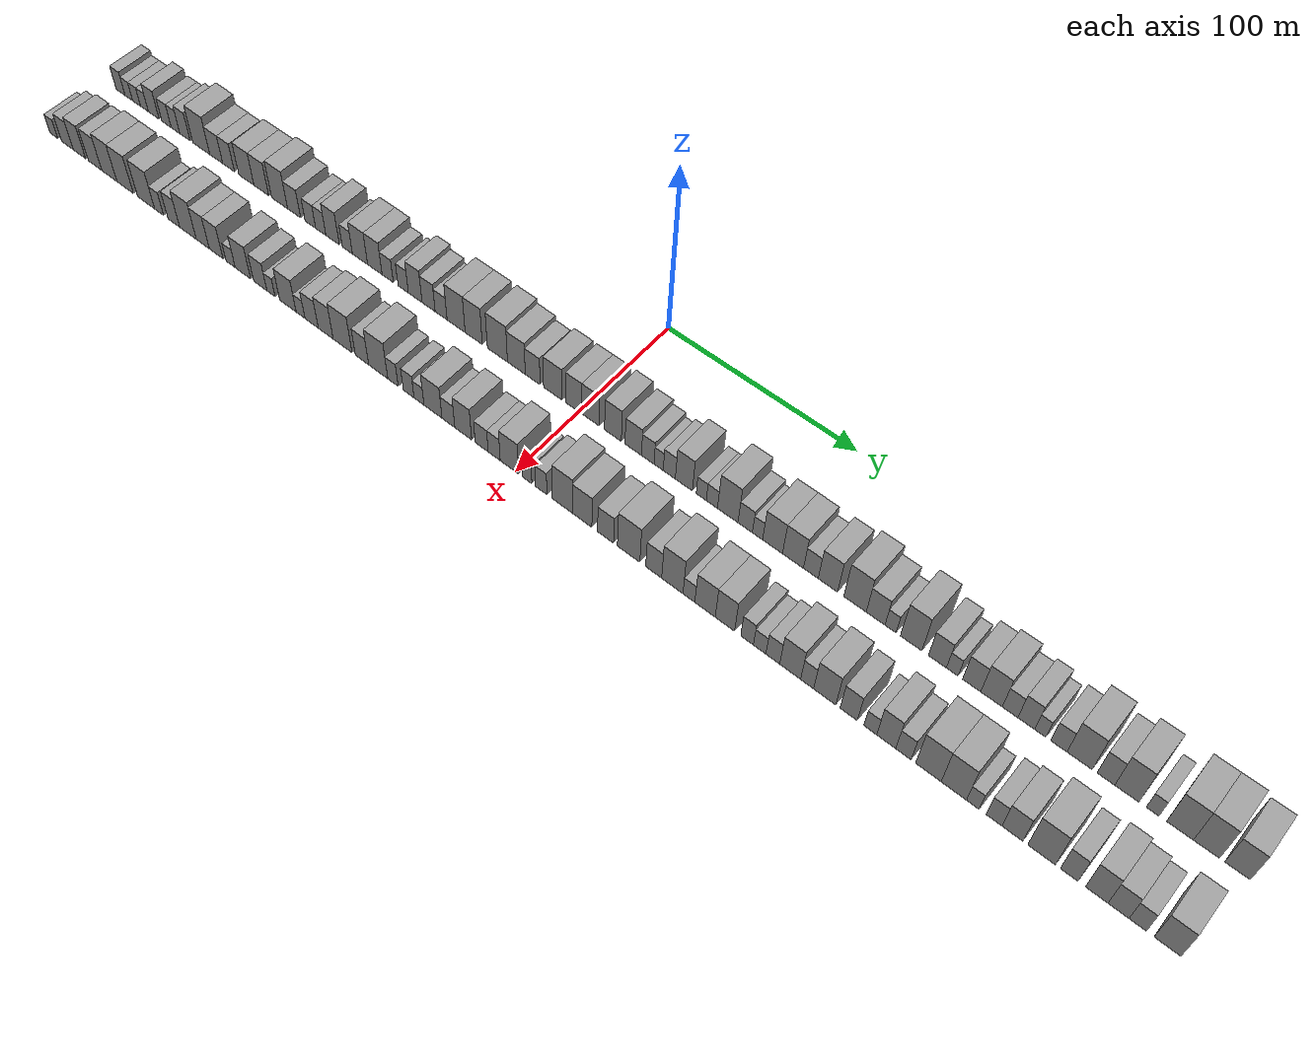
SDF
<sdf version="1.6">
 <world name="default">
  <scene>
   <sky><clouds><speed>12</speed></clouds></sky>
   <ambient>0.4 0.4 0.4 1</ambient>
   <background>0.7 0.7 0.7 1</background>
   <shadows>1</shadows>
  </scene>
  <gravity>0 0 -9.8066</gravity>
  <magnetic_field>6e-06 2.3e-05 -4.2e-05</magnetic_field>
  <physics default="0" name="default_physics" type="ode">
   <ode>
    <solver>
     <type>quick</type>
     <iters>10</iters>
     <sor>1.0</sor>
     <use_dynamic_moi_rescaling>0</use_dynamic_moi_rescaling>
    </solver>
    <constraints>
     <cfm>0</cfm>
     <erp>0.2</erp>
     <contact_max_correcting_vel>100</contact_max_correcting_vel>
     <contact_surface_layer>0.001</contact_surface_layer>
    </constraints>
   </ode>
   <max_step_size>0.004</max_step_size>
   <real_time_factor>1</real_time_factor>
   <real_time_update_rate>250</real_time_update_rate>
  </physics>
  <light name="sun" type="directional">
   <pose>0 0 10 0 0 0</pose>
   <diffuse>0.8 0.8 0.8 1</diffuse>
   <specular>0.2 0.2 0.2 1</specular>
   <attenuation>
    <range>1000</range>
    <constant>0.9</constant>
    <linear>0.01</linear>
    <quadratic>0.001</quadratic>
   </attenuation>
   <direction>-0.5 0.1 -0.9</direction>
  </light>
  <model name="building_1">
   <static>1</static>
   <pose>50.0000 -293.7207 0 0.000000 0.000000 0.000000</pose>
   <link name="link">
    <pose>0 0 7.50 0 0 0</pose>
    <collision name="collision"><geometry><box><size>20.0000 6.5586 15.0000</size></box></geometry></collision>
    <visual name="visual">
     <cast_shadows>0</cast_shadows>
     <geometry><box><size>20.0000 6.5586 15.0000</size></box></geometry>
     <material>
      <script>
       <uri>model://grey_wall/materials/scripts</uri>
       <uri>model://grey_wall/materials/textures</uri>
       <name>vrc/grey_wall</name>
      </script>
     </material>
    </visual>
   </link>
  </model>
  <model name="building_2">
   <static>1</static>
   <pose>50.0000 -287.6814 0 0.000000 0.000000 0.000000</pose>
   <link name="link">
    <pose>0 0 6.00 0 0 0</pose>
    <collision name="collision"><geometry><box><size>20.0000 5.5199 12.0000</size></box></geometry></collision>
    <visual name="visual">
     <cast_shadows>0</cast_shadows>
     <geometry><box><size>20.0000 5.5199 12.0000</size></box></geometry>
     <material>
      <script>
       <uri>model://grey_wall/materials/scripts</uri>
       <uri>model://grey_wall/materials/textures</uri>
       <name>vrc/grey_wall</name>
      </script>
     </material>
    </visual>
   </link>
  </model>
  <model name="building_3">
   <static>1</static>
   <pose>50.0000 -282.0184 0 0.000000 0.000000 0.000000</pose>
   <link name="link">
    <pose>0 0 6.00 0 0 0</pose>
    <collision name="collision"><geometry><box><size>20.0000 5.8060 12.0000</size></box></geometry></collision>
    <visual name="visual">
     <cast_shadows>0</cast_shadows>
     <geometry><box><size>20.0000 5.8060 12.0000</size></box></geometry>
     <material>
      <script>
       <uri>model://grey_wall/materials/scripts</uri>
       <uri>model://grey_wall/materials/textures</uri>
       <name>vrc/grey_wall</name>
      </script>
     </material>
    </visual>
   </link>
  </model>
  <model name="building_4">
   <static>1</static>
   <pose>50.0000 -276.2854 0 0.000000 0.000000 0.000000</pose>
   <link name="link">
    <pose>0 0 6.00 0 0 0</pose>
    <collision name="collision"><geometry><box><size>20.0000 5.6601 12.0000</size></box></geometry></collision>
    <visual name="visual">
     <cast_shadows>0</cast_shadows>
     <geometry><box><size>20.0000 5.6601 12.0000</size></box></geometry>
     <material>
      <script>
       <uri>model://grey_wall/materials/scripts</uri>
       <uri>model://grey_wall/materials/textures</uri>
       <name>vrc/grey_wall</name>
      </script>
     </material>
    </visual>
   </link>
  </model>
  <model name="building_5">
   <static>1</static>
   <pose>50.0000 -269.5465 0 0.000000 0.000000 0.000000</pose>
   <link name="link">
    <pose>0 0 9.00 0 0 0</pose>
    <collision name="collision"><geometry><box><size>20.0000 7.8177 18.0000</size></box></geometry></collision>
    <visual name="visual">
     <cast_shadows>0</cast_shadows>
     <geometry><box><size>20.0000 7.8177 18.0000</size></box></geometry>
     <material>
      <script>
       <uri>model://grey_wall/materials/scripts</uri>
       <uri>model://grey_wall/materials/textures</uri>
       <name>vrc/grey_wall</name>
      </script>
     </material>
    </visual>
   </link>
  </model>
  <model name="building_6">
   <static>1</static>
   <pose>50.0000 -260.2850 0 0.000000 0.000000 0.000000</pose>
   <link name="link">
    <pose>0 0 7.50 0 0 0</pose>
    <collision name="collision"><geometry><box><size>20.0000 6.7053 15.0000</size></box></geometry></collision>
    <visual name="visual">
     <cast_shadows>0</cast_shadows>
     <geometry><box><size>20.0000 6.7053 15.0000</size></box></geometry>
     <material>
      <script>
       <uri>model://grey_wall/materials/scripts</uri>
       <uri>model://grey_wall/materials/textures</uri>
       <name>vrc/grey_wall</name>
      </script>
     </material>
    </visual>
   </link>
  </model>
  <model name="building_7">
   <static>1</static>
   <pose>50.0000 -253.8806 0 0.000000 0.000000 0.000000</pose>
   <link name="link">
    <pose>0 0 7.50 0 0 0</pose>
    <collision name="collision"><geometry><box><size>20.0000 6.1035 15.0000</size></box></geometry></collision>
    <visual name="visual">
     <cast_shadows>0</cast_shadows>
     <geometry><box><size>20.0000 6.1035 15.0000</size></box></geometry>
     <material>
      <script>
       <uri>model://grey_wall/materials/scripts</uri>
       <uri>model://grey_wall/materials/textures</uri>
       <name>vrc/grey_wall</name>
      </script>
     </material>
    </visual>
   </link>
  </model>
  <model name="building_8">
   <static>1</static>
   <pose>50.0000 -247.1774 0 0.000000 0.000000 0.000000</pose>
   <link name="link">
    <pose>0 0 9.00 0 0 0</pose>
    <collision name="collision"><geometry><box><size>20.0000 7.3030 18.0000</size></box></geometry></collision>
    <visual name="visual">
     <cast_shadows>0</cast_shadows>
     <geometry><box><size>20.0000 7.3030 18.0000</size></box></geometry>
     <material>
      <script>
       <uri>model://grey_wall/materials/scripts</uri>
       <uri>model://grey_wall/materials/textures</uri>
       <name>vrc/grey_wall</name>
      </script>
     </material>
    </visual>
   </link>
  </model>
  <model name="building_9">
   <static>1</static>
   <pose>50.0000 -235.6194 0 0.000000 0.000000 0.000000</pose>
   <link name="link">
    <pose>0 0 12.00 0 0 0</pose>
    <collision name="collision"><geometry><box><size>20.0000 11.8131 24.0000</size></box></geometry></collision>
    <visual name="visual">
     <cast_shadows>0</cast_shadows>
     <geometry><box><size>20.0000 11.8131 24.0000</size></box></geometry>
     <material>
      <script>
       <uri>model://grey_wall/materials/scripts</uri>
       <uri>model://grey_wall/materials/textures</uri>
       <name>vrc/grey_wall</name>
      </script>
     </material>
    </visual>
   </link>
  </model>
  <model name="building_10">
   <static>1</static>
   <pose>50.0000 -225.2220 0 0.000000 0.000000 0.000000</pose>
   <link name="link">
    <pose>0 0 9.00 0 0 0</pose>
    <collision name="collision"><geometry><box><size>20.0000 8.9816 18.0000</size></box></geometry></collision>
    <visual name="visual">
     <cast_shadows>0</cast_shadows>
     <geometry><box><size>20.0000 8.9816 18.0000</size></box></geometry>
     <material>
      <script>
       <uri>model://grey_wall/materials/scripts</uri>
       <uri>model://grey_wall/materials/textures</uri>
       <name>vrc/grey_wall</name>
      </script>
     </material>
    </visual>
   </link>
  </model>
  <model name="building_11">
   <static>1</static>
   <pose>50.0000 -216.6811 0 0.000000 0.000000 0.000000</pose>
   <link name="link">
    <pose>0 0 9.00 0 0 0</pose>
    <collision name="collision"><geometry><box><size>20.0000 8.1002 18.0000</size></box></geometry></collision>
    <visual name="visual">
     <cast_shadows>0</cast_shadows>
     <geometry><box><size>20.0000 8.1002 18.0000</size></box></geometry>
     <material>
      <script>
       <uri>model://grey_wall/materials/scripts</uri>
       <uri>model://grey_wall/materials/textures</uri>
       <name>vrc/grey_wall</name>
      </script>
     </material>
    </visual>
   </link>
  </model>
  <model name="building_12">
   <static>1</static>
   <pose>50.0000 -204.4950 0 0.000000 0.000000 0.000000</pose>
   <link name="link">
    <pose>0 0 10.50 0 0 0</pose>
    <collision name="collision"><geometry><box><size>20.0000 10.2720 21.0000</size></box></geometry></collision>
    <visual name="visual">
     <cast_shadows>0</cast_shadows>
     <geometry><box><size>20.0000 10.2720 21.0000</size></box></geometry>
     <material>
      <script>
       <uri>model://grey_wall/materials/scripts</uri>
       <uri>model://grey_wall/materials/textures</uri>
       <name>vrc/grey_wall</name>
      </script>
     </material>
    </visual>
   </link>
  </model>
  <model name="building_13">
   <static>1</static>
   <pose>50.0000 -194.3998 0 0.000000 0.000000 0.000000</pose>
   <link name="link">
    <pose>0 0 10.50 0 0 0</pose>
    <collision name="collision"><geometry><box><size>20.0000 9.9184 21.0000</size></box></geometry></collision>
    <visual name="visual">
     <cast_shadows>0</cast_shadows>
     <geometry><box><size>20.0000 9.9184 21.0000</size></box></geometry>
     <material>
      <script>
       <uri>model://grey_wall/materials/scripts</uri>
       <uri>model://grey_wall/materials/textures</uri>
       <name>vrc/grey_wall</name>
      </script>
     </material>
    </visual>
   </link>
  </model>
  <model name="building_14">
   <static>1</static>
   <pose>50.0000 -182.0912 0 0.000000 0.000000 0.000000</pose>
   <link name="link">
    <pose>0 0 12.00 0 0 0</pose>
    <collision name="collision"><geometry><box><size>20.0000 10.6989 24.0000</size></box></geometry></collision>
    <visual name="visual">
     <cast_shadows>0</cast_shadows>
     <geometry><box><size>20.0000 10.6989 24.0000</size></box></geometry>
     <material>
      <script>
       <uri>model://grey_wall/materials/scripts</uri>
       <uri>model://grey_wall/materials/textures</uri>
       <name>vrc/grey_wall</name>
      </script>
     </material>
    </visual>
   </link>
  </model>
  <model name="building_15">
   <static>1</static>
   <pose>50.0000 -172.4970 0 0.000000 0.000000 0.000000</pose>
   <link name="link">
    <pose>0 0 9.00 0 0 0</pose>
    <collision name="collision"><geometry><box><size>20.0000 8.4894 18.0000</size></box></geometry></collision>
    <visual name="visual">
     <cast_shadows>0</cast_shadows>
     <geometry><box><size>20.0000 8.4894 18.0000</size></box></geometry>
     <material>
      <script>
       <uri>model://grey_wall/materials/scripts</uri>
       <uri>model://grey_wall/materials/textures</uri>
       <name>vrc/grey_wall</name>
      </script>
     </material>
    </visual>
   </link>
  </model>
  <model name="building_16">
   <static>1</static>
   <pose>50.0000 -161.8119 0 0.000000 0.000000 0.000000</pose>
   <link name="link">
    <pose>0 0 7.50 0 0 0</pose>
    <collision name="collision"><geometry><box><size>20.0000 6.8809 15.0000</size></box></geometry></collision>
    <visual name="visual">
     <cast_shadows>0</cast_shadows>
     <geometry><box><size>20.0000 6.8809 15.0000</size></box></geometry>
     <material>
      <script>
       <uri>model://grey_wall/materials/scripts</uri>
       <uri>model://grey_wall/materials/textures</uri>
       <name>vrc/grey_wall</name>
      </script>
     </material>
    </visual>
   </link>
  </model>
  <model name="building_17">
   <static>1</static>
   <pose>50.0000 -155.0350 0 0.000000 0.000000 0.000000</pose>
   <link name="link">
    <pose>0 0 7.50 0 0 0</pose>
    <collision name="collision"><geometry><box><size>20.0000 6.6728 15.0000</size></box></geometry></collision>
    <visual name="visual">
     <cast_shadows>0</cast_shadows>
     <geometry><box><size>20.0000 6.6728 15.0000</size></box></geometry>
     <material>
      <script>
       <uri>model://grey_wall/materials/scripts</uri>
       <uri>model://grey_wall/materials/textures</uri>
       <name>vrc/grey_wall</name>
      </script>
     </material>
    </visual>
   </link>
  </model>
  <model name="building_18">
   <static>1</static>
   <pose>50.0000 -147.3848 0 0.000000 0.000000 0.000000</pose>
   <link name="link">
    <pose>0 0 10.50 0 0 0</pose>
    <collision name="collision"><geometry><box><size>20.0000 8.6277 21.0000</size></box></geometry></collision>
    <visual name="visual">
     <cast_shadows>0</cast_shadows>
     <geometry><box><size>20.0000 8.6277 21.0000</size></box></geometry>
     <material>
      <script>
       <uri>model://grey_wall/materials/scripts</uri>
       <uri>model://grey_wall/materials/textures</uri>
       <name>vrc/grey_wall</name>
      </script>
     </material>
    </visual>
   </link>
  </model>
  <model name="building_19">
   <static>1</static>
   <pose>50.0000 -137.8836 0 0.000000 0.000000 0.000000</pose>
   <link name="link">
    <pose>0 0 7.50 0 0 0</pose>
    <collision name="collision"><geometry><box><size>20.0000 6.3746 15.0000</size></box></geometry></collision>
    <visual name="visual">
     <cast_shadows>0</cast_shadows>
     <geometry><box><size>20.0000 6.3746 15.0000</size></box></geometry>
     <material>
      <script>
       <uri>model://grey_wall/materials/scripts</uri>
       <uri>model://grey_wall/materials/textures</uri>
       <name>vrc/grey_wall</name>
      </script>
     </material>
    </visual>
   </link>
  </model>
  <model name="building_20">
   <static>1</static>
   <pose>50.0000 -129.8933 0 0.000000 0.000000 0.000000</pose>
   <link name="link">
    <pose>0 0 10.50 0 0 0</pose>
    <collision name="collision"><geometry><box><size>20.0000 9.6060 21.0000</size></box></geometry></collision>
    <visual name="visual">
     <cast_shadows>0</cast_shadows>
     <geometry><box><size>20.0000 9.6060 21.0000</size></box></geometry>
     <material>
      <script>
       <uri>model://grey_wall/materials/scripts</uri>
       <uri>model://grey_wall/materials/textures</uri>
       <name>vrc/grey_wall</name>
      </script>
     </material>
    </visual>
   </link>
  </model>
  <model name="building_21">
   <static>1</static>
   <pose>50.0000 -120.5425 0 0.000000 0.000000 0.000000</pose>
   <link name="link">
    <pose>0 0 10.50 0 0 0</pose>
    <collision name="collision"><geometry><box><size>20.0000 9.0956 21.0000</size></box></geometry></collision>
    <visual name="visual">
     <cast_shadows>0</cast_shadows>
     <geometry><box><size>20.0000 9.0956 21.0000</size></box></geometry>
     <material>
      <script>
       <uri>model://grey_wall/materials/scripts</uri>
       <uri>model://grey_wall/materials/textures</uri>
       <name>vrc/grey_wall</name>
      </script>
     </material>
    </visual>
   </link>
  </model>
  <model name="building_22">
   <static>1</static>
   <pose>50.0000 -112.5203 0 0.000000 0.000000 0.000000</pose>
   <link name="link">
    <pose>0 0 7.50 0 0 0</pose>
    <collision name="collision"><geometry><box><size>20.0000 6.9490 15.0000</size></box></geometry></collision>
    <visual name="visual">
     <cast_shadows>0</cast_shadows>
     <geometry><box><size>20.0000 6.9490 15.0000</size></box></geometry>
     <material>
      <script>
       <uri>model://grey_wall/materials/scripts</uri>
       <uri>model://grey_wall/materials/textures</uri>
       <name>vrc/grey_wall</name>
      </script>
     </material>
    </visual>
   </link>
  </model>
  <model name="building_23">
   <static>1</static>
   <pose>50.0000 -102.9059 0 0.000000 0.000000 0.000000</pose>
   <link name="link">
    <pose>0 0 7.50 0 0 0</pose>
    <collision name="collision"><geometry><box><size>20.0000 6.2797 15.0000</size></box></geometry></collision>
    <visual name="visual">
     <cast_shadows>0</cast_shadows>
     <geometry><box><size>20.0000 6.2797 15.0000</size></box></geometry>
     <material>
      <script>
       <uri>model://grey_wall/materials/scripts</uri>
       <uri>model://grey_wall/materials/textures</uri>
       <name>vrc/grey_wall</name>
      </script>
     </material>
    </visual>
   </link>
  </model>
  <model name="building_24">
   <static>1</static>
   <pose>50.0000 -95.5656 0 0.000000 0.000000 0.000000</pose>
   <link name="link">
    <pose>0 0 10.50 0 0 0</pose>
    <collision name="collision"><geometry><box><size>20.0000 8.4011 21.0000</size></box></geometry></collision>
    <visual name="visual">
     <cast_shadows>0</cast_shadows>
     <geometry><box><size>20.0000 8.4011 21.0000</size></box></geometry>
     <material>
      <script>
       <uri>model://grey_wall/materials/scripts</uri>
       <uri>model://grey_wall/materials/textures</uri>
       <name>vrc/grey_wall</name>
      </script>
     </material>
    </visual>
   </link>
  </model>
  <model name="building_25">
   <static>1</static>
   <pose>50.0000 -87.3929 0 0.000000 0.000000 0.000000</pose>
   <link name="link">
    <pose>0 0 9.00 0 0 0</pose>
    <collision name="collision"><geometry><box><size>20.0000 7.9442 18.0000</size></box></geometry></collision>
    <visual name="visual">
     <cast_shadows>0</cast_shadows>
     <geometry><box><size>20.0000 7.9442 18.0000</size></box></geometry>
     <material>
      <script>
       <uri>model://grey_wall/materials/scripts</uri>
       <uri>model://grey_wall/materials/textures</uri>
       <name>vrc/grey_wall</name>
      </script>
     </material>
    </visual>
   </link>
  </model>
  <model name="building_26">
   <static>1</static>
   <pose>50.0000 -79.8301 0 0.000000 0.000000 0.000000</pose>
   <link name="link">
    <pose>0 0 7.50 0 0 0</pose>
    <collision name="collision"><geometry><box><size>20.0000 7.1815 15.0000</size></box></geometry></collision>
    <visual name="visual">
     <cast_shadows>0</cast_shadows>
     <geometry><box><size>20.0000 7.1815 15.0000</size></box></geometry>
     <material>
      <script>
       <uri>model://grey_wall/materials/scripts</uri>
       <uri>model://grey_wall/materials/textures</uri>
       <name>vrc/grey_wall</name>
      </script>
     </material>
    </visual>
   </link>
  </model>
  <model name="building_27">
   <static>1</static>
   <pose>50.0000 -70.8516 0 0.000000 0.000000 0.000000</pose>
   <link name="link">
    <pose>0 0 12.00 0 0 0</pose>
    <collision name="collision"><geometry><box><size>20.0000 10.7755 24.0000</size></box></geometry></collision>
    <visual name="visual">
     <cast_shadows>0</cast_shadows>
     <geometry><box><size>20.0000 10.7755 24.0000</size></box></geometry>
     <material>
      <script>
       <uri>model://grey_wall/materials/scripts</uri>
       <uri>model://grey_wall/materials/textures</uri>
       <name>vrc/grey_wall</name>
      </script>
     </material>
    </visual>
   </link>
  </model>
  <model name="building_28">
   <static>1</static>
   <pose>50.0000 -60.4129 0 0.000000 0.000000 0.000000</pose>
   <link name="link">
    <pose>0 0 12.00 0 0 0</pose>
    <collision name="collision"><geometry><box><size>20.0000 10.1017 24.0000</size></box></geometry></collision>
    <visual name="visual">
     <cast_shadows>0</cast_shadows>
     <geometry><box><size>20.0000 10.1017 24.0000</size></box></geometry>
     <material>
      <script>
       <uri>model://grey_wall/materials/scripts</uri>
       <uri>model://grey_wall/materials/textures</uri>
       <name>vrc/grey_wall</name>
      </script>
     </material>
    </visual>
   </link>
  </model>
  <model name="building_29">
   <static>1</static>
   <pose>50.0000 -46.5263 0 0.000000 0.000000 0.000000</pose>
   <link name="link">
    <pose>0 0 12.00 0 0 0</pose>
    <collision name="collision"><geometry><box><size>20.0000 11.6716 24.0000</size></box></geometry></collision>
    <visual name="visual">
     <cast_shadows>0</cast_shadows>
     <geometry><box><size>20.0000 11.6716 24.0000</size></box></geometry>
     <material>
      <script>
       <uri>model://grey_wall/materials/scripts</uri>
       <uri>model://grey_wall/materials/textures</uri>
       <name>vrc/grey_wall</name>
      </script>
     </material>
    </visual>
   </link>
  </model>
  <model name="building_30">
   <static>1</static>
   <pose>50.0000 -35.5764 0 0.000000 0.000000 0.000000</pose>
   <link name="link">
    <pose>0 0 10.50 0 0 0</pose>
    <collision name="collision"><geometry><box><size>20.0000 10.2283 21.0000</size></box></geometry></collision>
    <visual name="visual">
     <cast_shadows>0</cast_shadows>
     <geometry><box><size>20.0000 10.2283 21.0000</size></box></geometry>
     <material>
      <script>
       <uri>model://grey_wall/materials/scripts</uri>
       <uri>model://grey_wall/materials/textures</uri>
       <name>vrc/grey_wall</name>
      </script>
     </material>
    </visual>
   </link>
  </model>
  <model name="building_31">
   <static>1</static>
   <pose>50.0000 -26.2525 0 0.000000 0.000000 0.000000</pose>
   <link name="link">
    <pose>0 0 9.00 0 0 0</pose>
    <collision name="collision"><geometry><box><size>20.0000 8.4193 18.0000</size></box></geometry></collision>
    <visual name="visual">
     <cast_shadows>0</cast_shadows>
     <geometry><box><size>20.0000 8.4193 18.0000</size></box></geometry>
     <material>
      <script>
       <uri>model://grey_wall/materials/scripts</uri>
       <uri>model://grey_wall/materials/textures</uri>
       <name>vrc/grey_wall</name>
      </script>
     </material>
    </visual>
   </link>
  </model>
  <model name="building_32">
   <static>1</static>
   <pose>50.0000 -14.8078 0 0.000000 0.000000 0.000000</pose>
   <link name="link">
    <pose>0 0 10.50 0 0 0</pose>
    <collision name="collision"><geometry><box><size>20.0000 10.4703 21.0000</size></box></geometry></collision>
    <visual name="visual">
     <cast_shadows>0</cast_shadows>
     <geometry><box><size>20.0000 10.4703 21.0000</size></box></geometry>
     <material>
      <script>
       <uri>model://grey_wall/materials/scripts</uri>
       <uri>model://grey_wall/materials/textures</uri>
       <name>vrc/grey_wall</name>
      </script>
     </material>
    </visual>
   </link>
  </model>
  <model name="building_33">
   <static>1</static>
   <pose>50.0000 -3.1432 0 0.000000 0.000000 0.000000</pose>
   <link name="link">
    <pose>0 0 10.50 0 0 0</pose>
    <collision name="collision"><geometry><box><size>20.0000 8.8589 21.0000</size></box></geometry></collision>
    <visual name="visual">
     <cast_shadows>0</cast_shadows>
     <geometry><box><size>20.0000 8.8589 21.0000</size></box></geometry>
     <material>
      <script>
       <uri>model://grey_wall/materials/scripts</uri>
       <uri>model://grey_wall/materials/textures</uri>
       <name>vrc/grey_wall</name>
      </script>
     </material>
    </visual>
   </link>
  </model>
  <model name="building_34">
   <static>1</static>
   <pose>50.0000 6.0466 0 0.000000 0.000000 0.000000</pose>
   <link name="link">
    <pose>0 0 10.50 0 0 0</pose>
    <collision name="collision"><geometry><box><size>20.0000 9.5208 21.0000</size></box></geometry></collision>
    <visual name="visual">
     <cast_shadows>0</cast_shadows>
     <geometry><box><size>20.0000 9.5208 21.0000</size></box></geometry>
     <material>
      <script>
       <uri>model://grey_wall/materials/scripts</uri>
       <uri>model://grey_wall/materials/textures</uri>
       <name>vrc/grey_wall</name>
      </script>
     </material>
    </visual>
   </link>
  </model>
  <model name="building_35">
   <static>1</static>
   <pose>50.0000 18.3578 0 0.000000 0.000000 0.000000</pose>
   <link name="link">
    <pose>0 0 10.50 0 0 0</pose>
    <collision name="collision"><geometry><box><size>20.0000 9.1016 21.0000</size></box></geometry></collision>
    <visual name="visual">
     <cast_shadows>0</cast_shadows>
     <geometry><box><size>20.0000 9.1016 21.0000</size></box></geometry>
     <material>
      <script>
       <uri>model://grey_wall/materials/scripts</uri>
       <uri>model://grey_wall/materials/textures</uri>
       <name>vrc/grey_wall</name>
      </script>
     </material>
    </visual>
   </link>
  </model>
  <model name="building_36">
   <static>1</static>
   <pose>50.0000 29.3276 0 0.000000 0.000000 0.000000</pose>
   <link name="link">
    <pose>0 0 9.00 0 0 0</pose>
    <collision name="collision"><geometry><box><size>20.0000 8.8378 18.0000</size></box></geometry></collision>
    <visual name="visual">
     <cast_shadows>0</cast_shadows>
     <geometry><box><size>20.0000 8.8378 18.0000</size></box></geometry>
     <material>
      <script>
       <uri>model://grey_wall/materials/scripts</uri>
       <uri>model://grey_wall/materials/textures</uri>
       <name>vrc/grey_wall</name>
      </script>
     </material>
    </visual>
   </link>
  </model>
  <model name="building_37">
   <static>1</static>
   <pose>50.0000 37.1012 0 0.000000 0.000000 0.000000</pose>
   <link name="link">
    <pose>0 0 7.50 0 0 0</pose>
    <collision name="collision"><geometry><box><size>20.0000 6.7094 15.0000</size></box></geometry></collision>
    <visual name="visual">
     <cast_shadows>0</cast_shadows>
     <geometry><box><size>20.0000 6.7094 15.0000</size></box></geometry>
     <material>
      <script>
       <uri>model://grey_wall/materials/scripts</uri>
       <uri>model://grey_wall/materials/textures</uri>
       <name>vrc/grey_wall</name>
      </script>
     </material>
    </visual>
   </link>
  </model>
  <model name="building_38">
   <static>1</static>
   <pose>50.0000 42.8789 0 0.000000 0.000000 0.000000</pose>
   <link name="link">
    <pose>0 0 6.00 0 0 0</pose>
    <collision name="collision"><geometry><box><size>20.0000 4.8460 12.0000</size></box></geometry></collision>
    <visual name="visual">
     <cast_shadows>0</cast_shadows>
     <geometry><box><size>20.0000 4.8460 12.0000</size></box></geometry>
     <material>
      <script>
       <uri>model://grey_wall/materials/scripts</uri>
       <uri>model://grey_wall/materials/textures</uri>
       <name>vrc/grey_wall</name>
      </script>
     </material>
    </visual>
   </link>
  </model>
  <model name="building_39">
   <static>1</static>
   <pose>50.0000 48.4959 0 0.000000 0.000000 0.000000</pose>
   <link name="link">
    <pose>0 0 7.50 0 0 0</pose>
    <collision name="collision"><geometry><box><size>20.0000 6.3881 15.0000</size></box></geometry></collision>
    <visual name="visual">
     <cast_shadows>0</cast_shadows>
     <geometry><box><size>20.0000 6.3881 15.0000</size></box></geometry>
     <material>
      <script>
       <uri>model://grey_wall/materials/scripts</uri>
       <uri>model://grey_wall/materials/textures</uri>
       <name>vrc/grey_wall</name>
      </script>
     </material>
    </visual>
   </link>
  </model>
  <model name="building_40">
   <static>1</static>
   <pose>50.0000 56.1326 0 0.000000 0.000000 0.000000</pose>
   <link name="link">
    <pose>0 0 10.50 0 0 0</pose>
    <collision name="collision"><geometry><box><size>20.0000 8.8852 21.0000</size></box></geometry></collision>
    <visual name="visual">
     <cast_shadows>0</cast_shadows>
     <geometry><box><size>20.0000 8.8852 21.0000</size></box></geometry>
     <material>
      <script>
       <uri>model://grey_wall/materials/scripts</uri>
       <uri>model://grey_wall/materials/textures</uri>
       <name>vrc/grey_wall</name>
      </script>
     </material>
    </visual>
   </link>
  </model>
  <model name="building_41">
   <static>1</static>
   <pose>50.0000 65.1850 0 0.000000 0.000000 0.000000</pose>
   <link name="link">
    <pose>0 0 6.00 0 0 0</pose>
    <collision name="collision"><geometry><box><size>20.0000 5.2195 12.0000</size></box></geometry></collision>
    <visual name="visual">
     <cast_shadows>0</cast_shadows>
     <geometry><box><size>20.0000 5.2195 12.0000</size></box></geometry>
     <material>
      <script>
       <uri>model://grey_wall/materials/scripts</uri>
       <uri>model://grey_wall/materials/textures</uri>
       <name>vrc/grey_wall</name>
      </script>
     </material>
    </visual>
   </link>
  </model>
  <model name="building_42">
   <static>1</static>
   <pose>50.0000 70.6543 0 0.000000 0.000000 0.000000</pose>
   <link name="link">
    <pose>0 0 6.00 0 0 0</pose>
    <collision name="collision"><geometry><box><size>20.0000 5.7191 12.0000</size></box></geometry></collision>
    <visual name="visual">
     <cast_shadows>0</cast_shadows>
     <geometry><box><size>20.0000 5.7191 12.0000</size></box></geometry>
     <material>
      <script>
       <uri>model://grey_wall/materials/scripts</uri>
       <uri>model://grey_wall/materials/textures</uri>
       <name>vrc/grey_wall</name>
      </script>
     </material>
    </visual>
   </link>
  </model>
  <model name="building_43">
   <static>1</static>
   <pose>50.0000 78.7085 0 0.000000 0.000000 0.000000</pose>
   <link name="link">
    <pose>0 0 12.00 0 0 0</pose>
    <collision name="collision"><geometry><box><size>20.0000 10.3895 24.0000</size></box></geometry></collision>
    <visual name="visual">
     <cast_shadows>0</cast_shadows>
     <geometry><box><size>20.0000 10.3895 24.0000</size></box></geometry>
     <material>
      <script>
       <uri>model://grey_wall/materials/scripts</uri>
       <uri>model://grey_wall/materials/textures</uri>
       <name>vrc/grey_wall</name>
      </script>
     </material>
    </visual>
   </link>
  </model>
  <model name="building_44">
   <static>1</static>
   <pose>50.0000 87.5398 0 0.000000 0.000000 0.000000</pose>
   <link name="link">
    <pose>0 0 7.50 0 0 0</pose>
    <collision name="collision"><geometry><box><size>20.0000 7.2731 15.0000</size></box></geometry></collision>
    <visual name="visual">
     <cast_shadows>0</cast_shadows>
     <geometry><box><size>20.0000 7.2731 15.0000</size></box></geometry>
     <material>
      <script>
       <uri>model://grey_wall/materials/scripts</uri>
       <uri>model://grey_wall/materials/textures</uri>
       <name>vrc/grey_wall</name>
      </script>
     </material>
    </visual>
   </link>
  </model>
  <model name="building_45">
   <static>1</static>
   <pose>50.0000 93.7264 0 0.000000 0.000000 0.000000</pose>
   <link name="link">
    <pose>0 0 6.00 0 0 0</pose>
    <collision name="collision"><geometry><box><size>20.0000 5.1001 12.0000</size></box></geometry></collision>
    <visual name="visual">
     <cast_shadows>0</cast_shadows>
     <geometry><box><size>20.0000 5.1001 12.0000</size></box></geometry>
     <material>
      <script>
       <uri>model://grey_wall/materials/scripts</uri>
       <uri>model://grey_wall/materials/textures</uri>
       <name>vrc/grey_wall</name>
      </script>
     </material>
    </visual>
   </link>
  </model>
  <model name="building_46">
   <static>1</static>
   <pose>50.0000 101.2266 0 0.000000 0.000000 0.000000</pose>
   <link name="link">
    <pose>0 0 10.50 0 0 0</pose>
    <collision name="collision"><geometry><box><size>20.0000 9.9003 21.0000</size></box></geometry></collision>
    <visual name="visual">
     <cast_shadows>0</cast_shadows>
     <geometry><box><size>20.0000 9.9003 21.0000</size></box></geometry>
     <material>
      <script>
       <uri>model://grey_wall/materials/scripts</uri>
       <uri>model://grey_wall/materials/textures</uri>
       <name>vrc/grey_wall</name>
      </script>
     </material>
    </visual>
   </link>
  </model>
  <model name="building_47">
   <static>1</static>
   <pose>50.0000 111.3244 0 0.000000 0.000000 0.000000</pose>
   <link name="link">
    <pose>0 0 10.50 0 0 0</pose>
    <collision name="collision"><geometry><box><size>20.0000 10.2953 21.0000</size></box></geometry></collision>
    <visual name="visual">
     <cast_shadows>0</cast_shadows>
     <geometry><box><size>20.0000 10.2953 21.0000</size></box></geometry>
     <material>
      <script>
       <uri>model://grey_wall/materials/scripts</uri>
       <uri>model://grey_wall/materials/textures</uri>
       <name>vrc/grey_wall</name>
      </script>
     </material>
    </visual>
   </link>
  </model>
  <model name="building_48">
   <static>1</static>
   <pose>50.0000 120.0511 0 0.000000 0.000000 0.000000</pose>
   <link name="link">
    <pose>0 0 7.50 0 0 0</pose>
    <collision name="collision"><geometry><box><size>20.0000 7.1583 15.0000</size></box></geometry></collision>
    <visual name="visual">
     <cast_shadows>0</cast_shadows>
     <geometry><box><size>20.0000 7.1583 15.0000</size></box></geometry>
     <material>
      <script>
       <uri>model://grey_wall/materials/scripts</uri>
       <uri>model://grey_wall/materials/textures</uri>
       <name>vrc/grey_wall</name>
      </script>
     </material>
    </visual>
   </link>
  </model>
  <model name="building_49">
   <static>1</static>
   <pose>50.0000 128.2841 0 0.000000 0.000000 0.000000</pose>
   <link name="link">
    <pose>0 0 10.50 0 0 0</pose>
    <collision name="collision"><geometry><box><size>20.0000 9.3077 21.0000</size></box></geometry></collision>
    <visual name="visual">
     <cast_shadows>0</cast_shadows>
     <geometry><box><size>20.0000 9.3077 21.0000</size></box></geometry>
     <material>
      <script>
       <uri>model://grey_wall/materials/scripts</uri>
       <uri>model://grey_wall/materials/textures</uri>
       <name>vrc/grey_wall</name>
      </script>
     </material>
    </visual>
   </link>
  </model>
  <model name="building_50">
   <static>1</static>
   <pose>50.0000 141.2554 0 0.000000 0.000000 0.000000</pose>
   <link name="link">
    <pose>0 0 12.00 0 0 0</pose>
    <collision name="collision"><geometry><box><size>20.0000 10.6349 24.0000</size></box></geometry></collision>
    <visual name="visual">
     <cast_shadows>0</cast_shadows>
     <geometry><box><size>20.0000 10.6349 24.0000</size></box></geometry>
     <material>
      <script>
       <uri>model://grey_wall/materials/scripts</uri>
       <uri>model://grey_wall/materials/textures</uri>
       <name>vrc/grey_wall</name>
      </script>
     </material>
    </visual>
   </link>
  </model>
  <model name="building_51">
   <static>1</static>
   <pose>50.0000 150.9640 0 0.000000 0.000000 0.000000</pose>
   <link name="link">
    <pose>0 0 9.00 0 0 0</pose>
    <collision name="collision"><geometry><box><size>20.0000 8.7823 18.0000</size></box></geometry></collision>
    <visual name="visual">
     <cast_shadows>0</cast_shadows>
     <geometry><box><size>20.0000 8.7823 18.0000</size></box></geometry>
     <material>
      <script>
       <uri>model://grey_wall/materials/scripts</uri>
       <uri>model://grey_wall/materials/textures</uri>
       <name>vrc/grey_wall</name>
      </script>
     </material>
    </visual>
   </link>
  </model>
  <model name="building_52">
   <static>1</static>
   <pose>50.0000 157.9376 0 0.000000 0.000000 0.000000</pose>
   <link name="link">
    <pose>0 0 6.00 0 0 0</pose>
    <collision name="collision"><geometry><box><size>20.0000 5.1650 12.0000</size></box></geometry></collision>
    <visual name="visual">
     <cast_shadows>0</cast_shadows>
     <geometry><box><size>20.0000 5.1650 12.0000</size></box></geometry>
     <material>
      <script>
       <uri>model://grey_wall/materials/scripts</uri>
       <uri>model://grey_wall/materials/textures</uri>
       <name>vrc/grey_wall</name>
      </script>
     </material>
    </visual>
   </link>
  </model>
  <model name="building_53">
   <static>1</static>
   <pose>50.0000 167.4618 0 0.000000 0.000000 0.000000</pose>
   <link name="link">
    <pose>0 0 12.00 0 0 0</pose>
    <collision name="collision"><geometry><box><size>20.0000 9.8834 24.0000</size></box></geometry></collision>
    <visual name="visual">
     <cast_shadows>0</cast_shadows>
     <geometry><box><size>20.0000 9.8834 24.0000</size></box></geometry>
     <material>
      <script>
       <uri>model://grey_wall/materials/scripts</uri>
       <uri>model://grey_wall/materials/textures</uri>
       <name>vrc/grey_wall</name>
      </script>
     </material>
    </visual>
   </link>
  </model>
  <model name="building_54">
   <static>1</static>
   <pose>50.0000 179.4813 0 0.000000 0.000000 0.000000</pose>
   <link name="link">
    <pose>0 0 9.00 0 0 0</pose>
    <collision name="collision"><geometry><box><size>20.0000 8.1556 18.0000</size></box></geometry></collision>
    <visual name="visual">
     <cast_shadows>0</cast_shadows>
     <geometry><box><size>20.0000 8.1556 18.0000</size></box></geometry>
     <material>
      <script>
       <uri>model://grey_wall/materials/scripts</uri>
       <uri>model://grey_wall/materials/textures</uri>
       <name>vrc/grey_wall</name>
      </script>
     </material>
    </visual>
   </link>
  </model>
  <model name="building_55">
   <static>1</static>
   <pose>50.0000 186.1787 0 0.000000 0.000000 0.000000</pose>
   <link name="link">
    <pose>0 0 6.00 0 0 0</pose>
    <collision name="collision"><geometry><box><size>20.0000 5.2392 12.0000</size></box></geometry></collision>
    <visual name="visual">
     <cast_shadows>0</cast_shadows>
     <geometry><box><size>20.0000 5.2392 12.0000</size></box></geometry>
     <material>
      <script>
       <uri>model://grey_wall/materials/scripts</uri>
       <uri>model://grey_wall/materials/textures</uri>
       <name>vrc/grey_wall</name>
      </script>
     </material>
    </visual>
   </link>
  </model>
  <model name="building_56">
   <static>1</static>
   <pose>50.0000 194.8588 0 0.000000 0.000000 0.000000</pose>
   <link name="link">
    <pose>0 0 9.00 0 0 0</pose>
    <collision name="collision"><geometry><box><size>20.0000 8.1209 18.0000</size></box></geometry></collision>
    <visual name="visual">
     <cast_shadows>0</cast_shadows>
     <geometry><box><size>20.0000 8.1209 18.0000</size></box></geometry>
     <material>
      <script>
       <uri>model://grey_wall/materials/scripts</uri>
       <uri>model://grey_wall/materials/textures</uri>
       <name>vrc/grey_wall</name>
      </script>
     </material>
    </visual>
   </link>
  </model>
  <model name="building_57">
   <static>1</static>
   <pose>50.0000 203.6728 0 0.000000 0.000000 0.000000</pose>
   <link name="link">
    <pose>0 0 10.50 0 0 0</pose>
    <collision name="collision"><geometry><box><size>20.0000 9.5072 21.0000</size></box></geometry></collision>
    <visual name="visual">
     <cast_shadows>0</cast_shadows>
     <geometry><box><size>20.0000 9.5072 21.0000</size></box></geometry>
     <material>
      <script>
       <uri>model://grey_wall/materials/scripts</uri>
       <uri>model://grey_wall/materials/textures</uri>
       <name>vrc/grey_wall</name>
      </script>
     </material>
    </visual>
   </link>
  </model>
  <model name="building_58">
   <static>1</static>
   <pose>50.0000 211.8074 0 0.000000 0.000000 0.000000</pose>
   <link name="link">
    <pose>0 0 7.50 0 0 0</pose>
    <collision name="collision"><geometry><box><size>20.0000 6.7619 15.0000</size></box></geometry></collision>
    <visual name="visual">
     <cast_shadows>0</cast_shadows>
     <geometry><box><size>20.0000 6.7619 15.0000</size></box></geometry>
     <material>
      <script>
       <uri>model://grey_wall/materials/scripts</uri>
       <uri>model://grey_wall/materials/textures</uri>
       <name>vrc/grey_wall</name>
      </script>
     </material>
    </visual>
   </link>
  </model>
  <model name="building_59">
   <static>1</static>
   <pose>50.0000 218.8079 0 0.000000 0.000000 0.000000</pose>
   <link name="link">
    <pose>0 0 9.00 0 0 0</pose>
    <collision name="collision"><geometry><box><size>20.0000 7.2391 18.0000</size></box></geometry></collision>
    <visual name="visual">
     <cast_shadows>0</cast_shadows>
     <geometry><box><size>20.0000 7.2391 18.0000</size></box></geometry>
     <material>
      <script>
       <uri>model://grey_wall/materials/scripts</uri>
       <uri>model://grey_wall/materials/textures</uri>
       <name>vrc/grey_wall</name>
      </script>
     </material>
    </visual>
   </link>
  </model>
  <model name="building_60">
   <static>1</static>
   <pose>50.0000 224.8794 0 0.000000 0.000000 0.000000</pose>
   <link name="link">
    <pose>0 0 6.00 0 0 0</pose>
    <collision name="collision"><geometry><box><size>20.0000 4.9039 12.0000</size></box></geometry></collision>
    <visual name="visual">
     <cast_shadows>0</cast_shadows>
     <geometry><box><size>20.0000 4.9039 12.0000</size></box></geometry>
     <material>
      <script>
       <uri>model://grey_wall/materials/scripts</uri>
       <uri>model://grey_wall/materials/textures</uri>
       <name>vrc/grey_wall</name>
      </script>
     </material>
    </visual>
   </link>
  </model>
  <model name="building_61">
   <static>1</static>
   <pose>50.0000 232.8269 0 0.000000 0.000000 0.000000</pose>
   <link name="link">
    <pose>0 0 7.50 0 0 0</pose>
    <collision name="collision"><geometry><box><size>20.0000 6.9911 15.0000</size></box></geometry></collision>
    <visual name="visual">
     <cast_shadows>0</cast_shadows>
     <geometry><box><size>20.0000 6.9911 15.0000</size></box></geometry>
     <material>
      <script>
       <uri>model://grey_wall/materials/scripts</uri>
       <uri>model://grey_wall/materials/textures</uri>
       <name>vrc/grey_wall</name>
      </script>
     </material>
    </visual>
   </link>
  </model>
  <model name="building_62">
   <static>1</static>
   <pose>50.0000 241.6393 0 0.000000 0.000000 0.000000</pose>
   <link name="link">
    <pose>0 0 12.00 0 0 0</pose>
    <collision name="collision"><geometry><box><size>20.0000 10.6336 24.0000</size></box></geometry></collision>
    <visual name="visual">
     <cast_shadows>0</cast_shadows>
     <geometry><box><size>20.0000 10.6336 24.0000</size></box></geometry>
     <material>
      <script>
       <uri>model://grey_wall/materials/scripts</uri>
       <uri>model://grey_wall/materials/textures</uri>
       <name>vrc/grey_wall</name>
      </script>
     </material>
    </visual>
   </link>
  </model>
  <model name="building_63">
   <static>1</static>
   <pose>50.0000 252.6410 0 0.000000 0.000000 0.000000</pose>
   <link name="link">
    <pose>0 0 9.00 0 0 0</pose>
    <collision name="collision"><geometry><box><size>20.0000 7.3699 18.0000</size></box></geometry></collision>
    <visual name="visual">
     <cast_shadows>0</cast_shadows>
     <geometry><box><size>20.0000 7.3699 18.0000</size></box></geometry>
     <material>
      <script>
       <uri>model://grey_wall/materials/scripts</uri>
       <uri>model://grey_wall/materials/textures</uri>
       <name>vrc/grey_wall</name>
      </script>
     </material>
    </visual>
   </link>
  </model>
  <model name="building_64">
   <static>1</static>
   <pose>50.0000 261.2885 0 0.000000 0.000000 0.000000</pose>
   <link name="link">
    <pose>0 0 12.00 0 0 0</pose>
    <collision name="collision"><geometry><box><size>20.0000 9.9250 24.0000</size></box></geometry></collision>
    <visual name="visual">
     <cast_shadows>0</cast_shadows>
     <geometry><box><size>20.0000 9.9250 24.0000</size></box></geometry>
     <material>
      <script>
       <uri>model://grey_wall/materials/scripts</uri>
       <uri>model://grey_wall/materials/textures</uri>
       <name>vrc/grey_wall</name>
      </script>
     </material>
    </visual>
   </link>
  </model>
  <model name="building_65">
   <static>1</static>
   <pose>50.0000 271.8575 0 0.000000 0.000000 0.000000</pose>
   <link name="link">
    <pose>0 0 6.00 0 0 0</pose>
    <collision name="collision"><geometry><box><size>20.0000 5.2131 12.0000</size></box></geometry></collision>
    <visual name="visual">
     <cast_shadows>0</cast_shadows>
     <geometry><box><size>20.0000 5.2131 12.0000</size></box></geometry>
     <material>
      <script>
       <uri>model://grey_wall/materials/scripts</uri>
       <uri>model://grey_wall/materials/textures</uri>
       <name>vrc/grey_wall</name>
      </script>
     </material>
    </visual>
   </link>
  </model>
  <model name="building_66">
   <static>1</static>
   <pose>50.0000 282.8292 0 0.000000 0.000000 0.000000</pose>
   <link name="link">
    <pose>0 0 12.00 0 0 0</pose>
    <collision name="collision"><geometry><box><size>20.0000 10.7302 24.0000</size></box></geometry></collision>
    <visual name="visual">
     <cast_shadows>0</cast_shadows>
     <geometry><box><size>20.0000 10.7302 24.0000</size></box></geometry>
     <material>
      <script>
       <uri>model://grey_wall/materials/scripts</uri>
       <uri>model://grey_wall/materials/textures</uri>
       <name>vrc/grey_wall</name>
      </script>
     </material>
    </visual>
   </link>
  </model>
  <model name="building_67">
   <static>1</static>
   <pose>50.0000 293.3667 0 0.000000 0.000000 0.000000</pose>
   <link name="link">
    <pose>0 0 12.00 0 0 0</pose>
    <collision name="collision"><geometry><box><size>20.0000 10.3449 24.0000</size></box></geometry></collision>
    <visual name="visual">
     <cast_shadows>0</cast_shadows>
     <geometry><box><size>20.0000 10.3449 24.0000</size></box></geometry>
     <material>
      <script>
       <uri>model://grey_wall/materials/scripts</uri>
       <uri>model://grey_wall/materials/textures</uri>
       <name>vrc/grey_wall</name>
      </script>
     </material>
    </visual>
   </link>
  </model>
  <model name="building_68">
   <static>1</static>
   <pose>50.0000 305.5257 0 0.000000 0.000000 0.000000</pose>
   <link name="link">
    <pose>0 0 10.50 0 0 0</pose>
    <collision name="collision"><geometry><box><size>20.0000 9.9730 21.0000</size></box></geometry></collision>
    <visual name="visual">
     <cast_shadows>0</cast_shadows>
     <geometry><box><size>20.0000 9.9730 21.0000</size></box></geometry>
     <material>
      <script>
       <uri>model://grey_wall/materials/scripts</uri>
       <uri>model://grey_wall/materials/textures</uri>
       <name>vrc/grey_wall</name>
      </script>
     </material>
    </visual>
   </link>
  </model>
  <model name="building_69">
   <static>1</static>
   <pose>90.0000 -295.1282 0 0.000000 0.000000 0.000000</pose>
   <link name="link">
    <pose>0 0 6.00 0 0 0</pose>
    <collision name="collision"><geometry><box><size>20.0000 5.7437 12.0000</size></box></geometry></collision>
    <visual name="visual">
     <cast_shadows>0</cast_shadows>
     <geometry><box><size>20.0000 5.7437 12.0000</size></box></geometry>
     <material>
      <script>
       <uri>model://grey_wall/materials/scripts</uri>
       <uri>model://grey_wall/materials/textures</uri>
       <name>vrc/grey_wall</name>
      </script>
     </material>
    </visual>
   </link>
  </model>
  <model name="building_70">
   <static>1</static>
   <pose>90.0000 -285.0855 0 0.000000 0.000000 0.000000</pose>
   <link name="link">
    <pose>0 0 9.00 0 0 0</pose>
    <collision name="collision"><geometry><box><size>20.0000 8.3417 18.0000</size></box></geometry></collision>
    <visual name="visual">
     <cast_shadows>0</cast_shadows>
     <geometry><box><size>20.0000 8.3417 18.0000</size></box></geometry>
     <material>
      <script>
       <uri>model://grey_wall/materials/scripts</uri>
       <uri>model://grey_wall/materials/textures</uri>
       <name>vrc/grey_wall</name>
      </script>
     </material>
    </visual>
   </link>
  </model>
  <model name="building_71">
   <static>1</static>
   <pose>90.0000 -276.3613 0 0.000000 0.000000 0.000000</pose>
   <link name="link">
    <pose>0 0 10.50 0 0 0</pose>
    <collision name="collision"><geometry><box><size>20.0000 9.1067 21.0000</size></box></geometry></collision>
    <visual name="visual">
     <cast_shadows>0</cast_shadows>
     <geometry><box><size>20.0000 9.1067 21.0000</size></box></geometry>
     <material>
      <script>
       <uri>model://grey_wall/materials/scripts</uri>
       <uri>model://grey_wall/materials/textures</uri>
       <name>vrc/grey_wall</name>
      </script>
     </material>
    </visual>
   </link>
  </model>
  <model name="building_72">
   <static>1</static>
   <pose>90.0000 -264.9593 0 0.000000 0.000000 0.000000</pose>
   <link name="link">
    <pose>0 0 10.50 0 0 0</pose>
    <collision name="collision"><geometry><box><size>20.0000 9.6972 21.0000</size></box></geometry></collision>
    <visual name="visual">
     <cast_shadows>0</cast_shadows>
     <geometry><box><size>20.0000 9.6972 21.0000</size></box></geometry>
     <material>
      <script>
       <uri>model://grey_wall/materials/scripts</uri>
       <uri>model://grey_wall/materials/textures</uri>
       <name>vrc/grey_wall</name>
      </script>
     </material>
    </visual>
   </link>
  </model>
  <model name="building_73">
   <static>1</static>
   <pose>90.0000 -254.7268 0 0.000000 0.000000 0.000000</pose>
   <link name="link">
    <pose>0 0 12.00 0 0 0</pose>
    <collision name="collision"><geometry><box><size>20.0000 10.7678 24.0000</size></box></geometry></collision>
    <visual name="visual">
     <cast_shadows>0</cast_shadows>
     <geometry><box><size>20.0000 10.7678 24.0000</size></box></geometry>
     <material>
      <script>
       <uri>model://grey_wall/materials/scripts</uri>
       <uri>model://grey_wall/materials/textures</uri>
       <name>vrc/grey_wall</name>
      </script>
     </material>
    </visual>
   </link>
  </model>
  <model name="building_74">
   <static>1</static>
   <pose>90.0000 -243.5399 0 0.000000 0.000000 0.000000</pose>
   <link name="link">
    <pose>0 0 12.00 0 0 0</pose>
    <collision name="collision"><geometry><box><size>20.0000 11.6060 24.0000</size></box></geometry></collision>
    <visual name="visual">
     <cast_shadows>0</cast_shadows>
     <geometry><box><size>20.0000 11.6060 24.0000</size></box></geometry>
     <material>
      <script>
       <uri>model://grey_wall/materials/scripts</uri>
       <uri>model://grey_wall/materials/textures</uri>
       <name>vrc/grey_wall</name>
      </script>
     </material>
    </visual>
   </link>
  </model>
  <model name="building_75">
   <static>1</static>
   <pose>90.0000 -228.8288 0 0.000000 0.000000 0.000000</pose>
   <link name="link">
    <pose>0 0 12.00 0 0 0</pose>
    <collision name="collision"><geometry><box><size>20.0000 11.8162 24.0000</size></box></geometry></collision>
    <visual name="visual">
     <cast_shadows>0</cast_shadows>
     <geometry><box><size>20.0000 11.8162 24.0000</size></box></geometry>
     <material>
      <script>
       <uri>model://grey_wall/materials/scripts</uri>
       <uri>model://grey_wall/materials/textures</uri>
       <name>vrc/grey_wall</name>
      </script>
     </material>
    </visual>
   </link>
  </model>
  <model name="building_76">
   <static>1</static>
   <pose>90.0000 -219.8242 0 0.000000 0.000000 0.000000</pose>
   <link name="link">
    <pose>0 0 7.50 0 0 0</pose>
    <collision name="collision"><geometry><box><size>20.0000 6.1930 15.0000</size></box></geometry></collision>
    <visual name="visual">
     <cast_shadows>0</cast_shadows>
     <geometry><box><size>20.0000 6.1930 15.0000</size></box></geometry>
     <material>
      <script>
       <uri>model://grey_wall/materials/scripts</uri>
       <uri>model://grey_wall/materials/textures</uri>
       <name>vrc/grey_wall</name>
      </script>
     </material>
    </visual>
   </link>
  </model>
  <model name="building_77">
   <static>1</static>
   <pose>90.0000 -209.7221 0 0.000000 0.000000 0.000000</pose>
   <link name="link">
    <pose>0 0 9.00 0 0 0</pose>
    <collision name="collision"><geometry><box><size>20.0000 8.0110 18.0000</size></box></geometry></collision>
    <visual name="visual">
     <cast_shadows>0</cast_shadows>
     <geometry><box><size>20.0000 8.0110 18.0000</size></box></geometry>
     <material>
      <script>
       <uri>model://grey_wall/materials/scripts</uri>
       <uri>model://grey_wall/materials/textures</uri>
       <name>vrc/grey_wall</name>
      </script>
     </material>
    </visual>
   </link>
  </model>
  <model name="building_78">
   <static>1</static>
   <pose>90.0000 -200.0910 0 0.000000 0.000000 0.000000</pose>
   <link name="link">
    <pose>0 0 12.00 0 0 0</pose>
    <collision name="collision"><geometry><box><size>20.0000 11.2513 24.0000</size></box></geometry></collision>
    <visual name="visual">
     <cast_shadows>0</cast_shadows>
     <geometry><box><size>20.0000 11.2513 24.0000</size></box></geometry>
     <material>
      <script>
       <uri>model://grey_wall/materials/scripts</uri>
       <uri>model://grey_wall/materials/textures</uri>
       <name>vrc/grey_wall</name>
      </script>
     </material>
    </visual>
   </link>
  </model>
  <model name="building_79">
   <static>1</static>
   <pose>90.0000 -190.0800 0 0.000000 0.000000 0.000000</pose>
   <link name="link">
    <pose>0 0 10.50 0 0 0</pose>
    <collision name="collision"><geometry><box><size>20.0000 8.7706 21.0000</size></box></geometry></collision>
    <visual name="visual">
     <cast_shadows>0</cast_shadows>
     <geometry><box><size>20.0000 8.7706 21.0000</size></box></geometry>
     <material>
      <script>
       <uri>model://grey_wall/materials/scripts</uri>
       <uri>model://grey_wall/materials/textures</uri>
       <name>vrc/grey_wall</name>
      </script>
     </material>
    </visual>
   </link>
  </model>
  <model name="building_80">
   <static>1</static>
   <pose>90.0000 -181.0978 0 0.000000 0.000000 0.000000</pose>
   <link name="link">
    <pose>0 0 10.50 0 0 0</pose>
    <collision name="collision"><geometry><box><size>20.0000 9.1938 21.0000</size></box></geometry></collision>
    <visual name="visual">
     <cast_shadows>0</cast_shadows>
     <geometry><box><size>20.0000 9.1938 21.0000</size></box></geometry>
     <material>
      <script>
       <uri>model://grey_wall/materials/scripts</uri>
       <uri>model://grey_wall/materials/textures</uri>
       <name>vrc/grey_wall</name>
      </script>
     </material>
    </visual>
   </link>
  </model>
  <model name="building_81">
   <static>1</static>
   <pose>90.0000 -171.5337 0 0.000000 0.000000 0.000000</pose>
   <link name="link">
    <pose>0 0 6.00 0 0 0</pose>
    <collision name="collision"><geometry><box><size>20.0000 5.9344 12.0000</size></box></geometry></collision>
    <visual name="visual">
     <cast_shadows>0</cast_shadows>
     <geometry><box><size>20.0000 5.9344 12.0000</size></box></geometry>
     <material>
      <script>
       <uri>model://grey_wall/materials/scripts</uri>
       <uri>model://grey_wall/materials/textures</uri>
       <name>vrc/grey_wall</name>
      </script>
     </material>
    </visual>
   </link>
  </model>
  <model name="building_82">
   <static>1</static>
   <pose>90.0000 -163.5370 0 0.000000 0.000000 0.000000</pose>
   <link name="link">
    <pose>0 0 10.50 0 0 0</pose>
    <collision name="collision"><geometry><box><size>20.0000 10.0590 21.0000</size></box></geometry></collision>
    <visual name="visual">
     <cast_shadows>0</cast_shadows>
     <geometry><box><size>20.0000 10.0590 21.0000</size></box></geometry>
     <material>
      <script>
       <uri>model://grey_wall/materials/scripts</uri>
       <uri>model://grey_wall/materials/textures</uri>
       <name>vrc/grey_wall</name>
      </script>
     </material>
    </visual>
   </link>
  </model>
  <model name="building_83">
   <static>1</static>
   <pose>90.0000 -152.2550 0 0.000000 0.000000 0.000000</pose>
   <link name="link">
    <pose>0 0 9.00 0 0 0</pose>
    <collision name="collision"><geometry><box><size>20.0000 8.5050 18.0000</size></box></geometry></collision>
    <visual name="visual">
     <cast_shadows>0</cast_shadows>
     <geometry><box><size>20.0000 8.5050 18.0000</size></box></geometry>
     <material>
      <script>
       <uri>model://grey_wall/materials/scripts</uri>
       <uri>model://grey_wall/materials/textures</uri>
       <name>vrc/grey_wall</name>
      </script>
     </material>
    </visual>
   </link>
  </model>
  <model name="building_84">
   <static>1</static>
   <pose>90.0000 -145.3968 0 0.000000 0.000000 0.000000</pose>
   <link name="link">
    <pose>0 0 6.00 0 0 0</pose>
    <collision name="collision"><geometry><box><size>20.0000 5.2114 12.0000</size></box></geometry></collision>
    <visual name="visual">
     <cast_shadows>0</cast_shadows>
     <geometry><box><size>20.0000 5.2114 12.0000</size></box></geometry>
     <material>
      <script>
       <uri>model://grey_wall/materials/scripts</uri>
       <uri>model://grey_wall/materials/textures</uri>
       <name>vrc/grey_wall</name>
      </script>
     </material>
    </visual>
   </link>
  </model>
  <model name="building_85">
   <static>1</static>
   <pose>90.0000 -134.5724 0 0.000000 0.000000 0.000000</pose>
   <link name="link">
    <pose>0 0 10.50 0 0 0</pose>
    <collision name="collision"><geometry><box><size>20.0000 10.4373 21.0000</size></box></geometry></collision>
    <visual name="visual">
     <cast_shadows>0</cast_shadows>
     <geometry><box><size>20.0000 10.4373 21.0000</size></box></geometry>
     <material>
      <script>
       <uri>model://grey_wall/materials/scripts</uri>
       <uri>model://grey_wall/materials/textures</uri>
       <name>vrc/grey_wall</name>
      </script>
     </material>
    </visual>
   </link>
  </model>
  <model name="building_86">
   <static>1</static>
   <pose>90.0000 -126.5986 0 0.000000 0.000000 0.000000</pose>
   <link name="link">
    <pose>0 0 6.00 0 0 0</pose>
    <collision name="collision"><geometry><box><size>20.0000 5.5104 12.0000</size></box></geometry></collision>
    <visual name="visual">
     <cast_shadows>0</cast_shadows>
     <geometry><box><size>20.0000 5.5104 12.0000</size></box></geometry>
     <material>
      <script>
       <uri>model://grey_wall/materials/scripts</uri>
       <uri>model://grey_wall/materials/textures</uri>
       <name>vrc/grey_wall</name>
      </script>
     </material>
    </visual>
   </link>
  </model>
  <model name="building_87">
   <static>1</static>
   <pose>90.0000 -119.6577 0 0.000000 0.000000 0.000000</pose>
   <link name="link">
    <pose>0 0 9.00 0 0 0</pose>
    <collision name="collision"><geometry><box><size>20.0000 8.3714 18.0000</size></box></geometry></collision>
    <visual name="visual">
     <cast_shadows>0</cast_shadows>
     <geometry><box><size>20.0000 8.3714 18.0000</size></box></geometry>
     <material>
      <script>
       <uri>model://grey_wall/materials/scripts</uri>
       <uri>model://grey_wall/materials/textures</uri>
       <name>vrc/grey_wall</name>
      </script>
     </material>
    </visual>
   </link>
  </model>
  <model name="building_88">
   <static>1</static>
   <pose>90.0000 -110.8665 0 0.000000 0.000000 0.000000</pose>
   <link name="link">
    <pose>0 0 10.50 0 0 0</pose>
    <collision name="collision"><geometry><box><size>20.0000 9.2111 21.0000</size></box></geometry></collision>
    <visual name="visual">
     <cast_shadows>0</cast_shadows>
     <geometry><box><size>20.0000 9.2111 21.0000</size></box></geometry>
     <material>
      <script>
       <uri>model://grey_wall/materials/scripts</uri>
       <uri>model://grey_wall/materials/textures</uri>
       <name>vrc/grey_wall</name>
      </script>
     </material>
    </visual>
   </link>
  </model>
  <model name="building_89">
   <static>1</static>
   <pose>90.0000 -100.5035 0 0.000000 0.000000 0.000000</pose>
   <link name="link">
    <pose>0 0 12.00 0 0 0</pose>
    <collision name="collision"><geometry><box><size>20.0000 11.5151 24.0000</size></box></geometry></collision>
    <visual name="visual">
     <cast_shadows>0</cast_shadows>
     <geometry><box><size>20.0000 11.5151 24.0000</size></box></geometry>
     <material>
      <script>
       <uri>model://grey_wall/materials/scripts</uri>
       <uri>model://grey_wall/materials/textures</uri>
       <name>vrc/grey_wall</name>
      </script>
     </material>
    </visual>
   </link>
  </model>
  <model name="building_90">
   <static>1</static>
   <pose>90.0000 -88.7004 0 0.000000 0.000000 0.000000</pose>
   <link name="link">
    <pose>0 0 9.00 0 0 0</pose>
    <collision name="collision"><geometry><box><size>20.0000 8.0909 18.0000</size></box></geometry></collision>
    <visual name="visual">
     <cast_shadows>0</cast_shadows>
     <geometry><box><size>20.0000 8.0909 18.0000</size></box></geometry>
     <material>
      <script>
       <uri>model://grey_wall/materials/scripts</uri>
       <uri>model://grey_wall/materials/textures</uri>
       <name>vrc/grey_wall</name>
      </script>
     </material>
    </visual>
   </link>
  </model>
  <model name="building_91">
   <static>1</static>
   <pose>90.0000 -78.9290 0 0.000000 0.000000 0.000000</pose>
   <link name="link">
    <pose>0 0 12.00 0 0 0</pose>
    <collision name="collision"><geometry><box><size>20.0000 11.4519 24.0000</size></box></geometry></collision>
    <visual name="visual">
     <cast_shadows>0</cast_shadows>
     <geometry><box><size>20.0000 11.4519 24.0000</size></box></geometry>
     <material>
      <script>
       <uri>model://grey_wall/materials/scripts</uri>
       <uri>model://grey_wall/materials/textures</uri>
       <name>vrc/grey_wall</name>
      </script>
     </material>
    </visual>
   </link>
  </model>
  <model name="building_92">
   <static>1</static>
   <pose>90.0000 -70.1134 0 0.000000 0.000000 0.000000</pose>
   <link name="link">
    <pose>0 0 7.50 0 0 0</pose>
    <collision name="collision"><geometry><box><size>20.0000 6.1793 15.0000</size></box></geometry></collision>
    <visual name="visual">
     <cast_shadows>0</cast_shadows>
     <geometry><box><size>20.0000 6.1793 15.0000</size></box></geometry>
     <material>
      <script>
       <uri>model://grey_wall/materials/scripts</uri>
       <uri>model://grey_wall/materials/textures</uri>
       <name>vrc/grey_wall</name>
      </script>
     </material>
    </visual>
   </link>
  </model>
  <model name="building_93">
   <static>1</static>
   <pose>90.0000 -60.8560 0 0.000000 0.000000 0.000000</pose>
   <link name="link">
    <pose>0 0 7.50 0 0 0</pose>
    <collision name="collision"><geometry><box><size>20.0000 6.3354 15.0000</size></box></geometry></collision>
    <visual name="visual">
     <cast_shadows>0</cast_shadows>
     <geometry><box><size>20.0000 6.3354 15.0000</size></box></geometry>
     <material>
      <script>
       <uri>model://grey_wall/materials/scripts</uri>
       <uri>model://grey_wall/materials/textures</uri>
       <name>vrc/grey_wall</name>
      </script>
     </material>
    </visual>
   </link>
  </model>
  <model name="building_94">
   <static>1</static>
   <pose>90.0000 -54.7926 0 0.000000 0.000000 0.000000</pose>
   <link name="link">
    <pose>0 0 6.00 0 0 0</pose>
    <collision name="collision"><geometry><box><size>20.0000 5.7915 12.0000</size></box></geometry></collision>
    <visual name="visual">
     <cast_shadows>0</cast_shadows>
     <geometry><box><size>20.0000 5.7915 12.0000</size></box></geometry>
     <material>
      <script>
       <uri>model://grey_wall/materials/scripts</uri>
       <uri>model://grey_wall/materials/textures</uri>
       <name>vrc/grey_wall</name>
      </script>
     </material>
    </visual>
   </link>
  </model>
  <model name="building_95">
   <static>1</static>
   <pose>90.0000 -46.6921 0 0.000000 0.000000 0.000000</pose>
   <link name="link">
    <pose>0 0 10.50 0 0 0</pose>
    <collision name="collision"><geometry><box><size>20.0000 10.4095 21.0000</size></box></geometry></collision>
    <visual name="visual">
     <cast_shadows>0</cast_shadows>
     <geometry><box><size>20.0000 10.4095 21.0000</size></box></geometry>
     <material>
      <script>
       <uri>model://grey_wall/materials/scripts</uri>
       <uri>model://grey_wall/materials/textures</uri>
       <name>vrc/grey_wall</name>
      </script>
     </material>
    </visual>
   </link>
  </model>
  <model name="building_96">
   <static>1</static>
   <pose>90.0000 -37.8104 0 0.000000 0.000000 0.000000</pose>
   <link name="link">
    <pose>0 0 7.50 0 0 0</pose>
    <collision name="collision"><geometry><box><size>20.0000 7.3540 15.0000</size></box></geometry></collision>
    <visual name="visual">
     <cast_shadows>0</cast_shadows>
     <geometry><box><size>20.0000 7.3540 15.0000</size></box></geometry>
     <material>
      <script>
       <uri>model://grey_wall/materials/scripts</uri>
       <uri>model://grey_wall/materials/textures</uri>
       <name>vrc/grey_wall</name>
      </script>
     </material>
    </visual>
   </link>
  </model>
  <model name="building_97">
   <static>1</static>
   <pose>90.0000 -29.3366 0 0.000000 0.000000 0.000000</pose>
   <link name="link">
    <pose>0 0 10.50 0 0 0</pose>
    <collision name="collision"><geometry><box><size>20.0000 9.5937 21.0000</size></box></geometry></collision>
    <visual name="visual">
     <cast_shadows>0</cast_shadows>
     <geometry><box><size>20.0000 9.5937 21.0000</size></box></geometry>
     <material>
      <script>
       <uri>model://grey_wall/materials/scripts</uri>
       <uri>model://grey_wall/materials/textures</uri>
       <name>vrc/grey_wall</name>
      </script>
     </material>
    </visual>
   </link>
  </model>
  <model name="building_98">
   <static>1</static>
   <pose>90.0000 -18.9186 0 0.000000 0.000000 0.000000</pose>
   <link name="link">
    <pose>0 0 7.50 0 0 0</pose>
    <collision name="collision"><geometry><box><size>20.0000 7.2422 15.0000</size></box></geometry></collision>
    <visual name="visual">
     <cast_shadows>0</cast_shadows>
     <geometry><box><size>20.0000 7.2422 15.0000</size></box></geometry>
     <material>
      <script>
       <uri>model://grey_wall/materials/scripts</uri>
       <uri>model://grey_wall/materials/textures</uri>
       <name>vrc/grey_wall</name>
      </script>
     </material>
    </visual>
   </link>
  </model>
  <model name="building_99">
   <static>1</static>
   <pose>90.0000 -11.9321 0 0.000000 0.000000 0.000000</pose>
   <link name="link">
    <pose>0 0 7.50 0 0 0</pose>
    <collision name="collision"><geometry><box><size>20.0000 6.7309 15.0000</size></box></geometry></collision>
    <visual name="visual">
     <cast_shadows>0</cast_shadows>
     <geometry><box><size>20.0000 6.7309 15.0000</size></box></geometry>
     <material>
      <script>
       <uri>model://grey_wall/materials/scripts</uri>
       <uri>model://grey_wall/materials/textures</uri>
       <name>vrc/grey_wall</name>
      </script>
     </material>
    </visual>
   </link>
  </model>
  <model name="building_100">
   <static>1</static>
   <pose>90.0000 -3.4724 0 0.000000 0.000000 0.000000</pose>
   <link name="link">
    <pose>0 0 10.50 0 0 0</pose>
    <collision name="collision"><geometry><box><size>20.0000 10.1885 21.0000</size></box></geometry></collision>
    <visual name="visual">
     <cast_shadows>0</cast_shadows>
     <geometry><box><size>20.0000 10.1885 21.0000</size></box></geometry>
     <material>
      <script>
       <uri>model://grey_wall/materials/scripts</uri>
       <uri>model://grey_wall/materials/textures</uri>
       <name>vrc/grey_wall</name>
      </script>
     </material>
    </visual>
   </link>
  </model>
  <model name="building_101">
   <static>1</static>
   <pose>90.0000 6.2363 0 0.000000 0.000000 0.000000</pose>
   <link name="link">
    <pose>0 0 6.00 0 0 0</pose>
    <collision name="collision"><geometry><box><size>20.0000 5.2288 12.0000</size></box></geometry></collision>
    <visual name="visual">
     <cast_shadows>0</cast_shadows>
     <geometry><box><size>20.0000 5.2288 12.0000</size></box></geometry>
     <material>
      <script>
       <uri>model://grey_wall/materials/scripts</uri>
       <uri>model://grey_wall/materials/textures</uri>
       <name>vrc/grey_wall</name>
      </script>
     </material>
    </visual>
   </link>
  </model>
  <model name="building_102">
   <static>1</static>
   <pose>90.0000 13.9206 0 0.000000 0.000000 0.000000</pose>
   <link name="link">
    <pose>0 0 7.50 0 0 0</pose>
    <collision name="collision"><geometry><box><size>20.0000 6.1398 15.0000</size></box></geometry></collision>
    <visual name="visual">
     <cast_shadows>0</cast_shadows>
     <geometry><box><size>20.0000 6.1398 15.0000</size></box></geometry>
     <material>
      <script>
       <uri>model://grey_wall/materials/scripts</uri>
       <uri>model://grey_wall/materials/textures</uri>
       <name>vrc/grey_wall</name>
      </script>
     </material>
    </visual>
   </link>
  </model>
  <model name="building_103">
   <static>1</static>
   <pose>90.0000 25.3450 0 0.000000 0.000000 0.000000</pose>
   <link name="link">
    <pose>0 0 12.00 0 0 0</pose>
    <collision name="collision"><geometry><box><size>20.0000 10.7088 24.0000</size></box></geometry></collision>
    <visual name="visual">
     <cast_shadows>0</cast_shadows>
     <geometry><box><size>20.0000 10.7088 24.0000</size></box></geometry>
     <material>
      <script>
       <uri>model://grey_wall/materials/scripts</uri>
       <uri>model://grey_wall/materials/textures</uri>
       <name>vrc/grey_wall</name>
      </script>
     </material>
    </visual>
   </link>
  </model>
  <model name="building_104">
   <static>1</static>
   <pose>90.0000 35.8431 0 0.000000 0.000000 0.000000</pose>
   <link name="link">
    <pose>0 0 10.50 0 0 0</pose>
    <collision name="collision"><geometry><box><size>20.0000 10.2875 21.0000</size></box></geometry></collision>
    <visual name="visual">
     <cast_shadows>0</cast_shadows>
     <geometry><box><size>20.0000 10.2875 21.0000</size></box></geometry>
     <material>
      <script>
       <uri>model://grey_wall/materials/scripts</uri>
       <uri>model://grey_wall/materials/textures</uri>
       <name>vrc/grey_wall</name>
      </script>
     </material>
    </visual>
   </link>
  </model>
  <model name="building_105">
   <static>1</static>
   <pose>90.0000 48.1673 0 0.000000 0.000000 0.000000</pose>
   <link name="link">
    <pose>0 0 9.00 0 0 0</pose>
    <collision name="collision"><geometry><box><size>20.0000 8.3607 18.0000</size></box></geometry></collision>
    <visual name="visual">
     <cast_shadows>0</cast_shadows>
     <geometry><box><size>20.0000 8.3607 18.0000</size></box></geometry>
     <material>
      <script>
       <uri>model://grey_wall/materials/scripts</uri>
       <uri>model://grey_wall/materials/textures</uri>
       <name>vrc/grey_wall</name>
      </script>
     </material>
    </visual>
   </link>
  </model>
  <model name="building_106">
   <static>1</static>
   <pose>90.0000 60.1326 0 0.000000 0.000000 0.000000</pose>
   <link name="link">
    <pose>0 0 12.00 0 0 0</pose>
    <collision name="collision"><geometry><box><size>20.0000 11.5699 24.0000</size></box></geometry></collision>
    <visual name="visual">
     <cast_shadows>0</cast_shadows>
     <geometry><box><size>20.0000 11.5699 24.0000</size></box></geometry>
     <material>
      <script>
       <uri>model://grey_wall/materials/scripts</uri>
       <uri>model://grey_wall/materials/textures</uri>
       <name>vrc/grey_wall</name>
      </script>
     </material>
    </visual>
   </link>
  </model>
  <model name="building_107">
   <static>1</static>
   <pose>90.0000 72.9621 0 0.000000 0.000000 0.000000</pose>
   <link name="link">
    <pose>0 0 9.00 0 0 0</pose>
    <collision name="collision"><geometry><box><size>20.0000 8.0892 18.0000</size></box></geometry></collision>
    <visual name="visual">
     <cast_shadows>0</cast_shadows>
     <geometry><box><size>20.0000 8.0892 18.0000</size></box></geometry>
     <material>
      <script>
       <uri>model://grey_wall/materials/scripts</uri>
       <uri>model://grey_wall/materials/textures</uri>
       <name>vrc/grey_wall</name>
      </script>
     </material>
    </visual>
   </link>
  </model>
  <model name="building_108">
   <static>1</static>
   <pose>90.0000 82.3619 0 0.000000 0.000000 0.000000</pose>
   <link name="link">
    <pose>0 0 12.00 0 0 0</pose>
    <collision name="collision"><geometry><box><size>20.0000 10.7104 24.0000</size></box></geometry></collision>
    <visual name="visual">
     <cast_shadows>0</cast_shadows>
     <geometry><box><size>20.0000 10.7104 24.0000</size></box></geometry>
     <material>
      <script>
       <uri>model://grey_wall/materials/scripts</uri>
       <uri>model://grey_wall/materials/textures</uri>
       <name>vrc/grey_wall</name>
      </script>
     </material>
    </visual>
   </link>
  </model>
  <model name="building_109">
   <static>1</static>
   <pose>90.0000 90.6611 0 0.000000 0.000000 0.000000</pose>
   <link name="link">
    <pose>0 0 6.00 0 0 0</pose>
    <collision name="collision"><geometry><box><size>20.0000 5.8879 12.0000</size></box></geometry></collision>
    <visual name="visual">
     <cast_shadows>0</cast_shadows>
     <geometry><box><size>20.0000 5.8879 12.0000</size></box></geometry>
     <material>
      <script>
       <uri>model://grey_wall/materials/scripts</uri>
       <uri>model://grey_wall/materials/textures</uri>
       <name>vrc/grey_wall</name>
      </script>
     </material>
    </visual>
   </link>
  </model>
  <model name="building_110">
   <static>1</static>
   <pose>90.0000 98.6370 0 0.000000 0.000000 0.000000</pose>
   <link name="link">
    <pose>0 0 10.50 0 0 0</pose>
    <collision name="collision"><geometry><box><size>20.0000 10.0638 21.0000</size></box></geometry></collision>
    <visual name="visual">
     <cast_shadows>0</cast_shadows>
     <geometry><box><size>20.0000 10.0638 21.0000</size></box></geometry>
     <material>
      <script>
       <uri>model://grey_wall/materials/scripts</uri>
       <uri>model://grey_wall/materials/textures</uri>
       <name>vrc/grey_wall</name>
      </script>
     </material>
    </visual>
   </link>
  </model>
  <model name="building_111">
   <static>1</static>
   <pose>90.0000 108.3869 0 0.000000 0.000000 0.000000</pose>
   <link name="link">
    <pose>0 0 10.50 0 0 0</pose>
    <collision name="collision"><geometry><box><size>20.0000 9.4360 21.0000</size></box></geometry></collision>
    <visual name="visual">
     <cast_shadows>0</cast_shadows>
     <geometry><box><size>20.0000 9.4360 21.0000</size></box></geometry>
     <material>
      <script>
       <uri>model://grey_wall/materials/scripts</uri>
       <uri>model://grey_wall/materials/textures</uri>
       <name>vrc/grey_wall</name>
      </script>
     </material>
    </visual>
   </link>
  </model>
  <model name="building_112">
   <static>1</static>
   <pose>90.0000 119.1475 0 0.000000 0.000000 0.000000</pose>
   <link name="link">
    <pose>0 0 7.50 0 0 0</pose>
    <collision name="collision"><geometry><box><size>20.0000 6.0852 15.0000</size></box></geometry></collision>
    <visual name="visual">
     <cast_shadows>0</cast_shadows>
     <geometry><box><size>20.0000 6.0852 15.0000</size></box></geometry>
     <material>
      <script>
       <uri>model://grey_wall/materials/scripts</uri>
       <uri>model://grey_wall/materials/textures</uri>
       <name>vrc/grey_wall</name>
      </script>
     </material>
    </visual>
   </link>
  </model>
  <model name="building_113">
   <static>1</static>
   <pose>90.0000 125.1614 0 0.000000 0.000000 0.000000</pose>
   <link name="link">
    <pose>0 0 6.00 0 0 0</pose>
    <collision name="collision"><geometry><box><size>20.0000 5.9427 12.0000</size></box></geometry></collision>
    <visual name="visual">
     <cast_shadows>0</cast_shadows>
     <geometry><box><size>20.0000 5.9427 12.0000</size></box></geometry>
     <material>
      <script>
       <uri>model://grey_wall/materials/scripts</uri>
       <uri>model://grey_wall/materials/textures</uri>
       <name>vrc/grey_wall</name>
      </script>
     </material>
    </visual>
   </link>
  </model>
  <model name="building_114">
   <static>1</static>
   <pose>90.0000 131.4122 0 0.000000 0.000000 0.000000</pose>
   <link name="link">
    <pose>0 0 7.50 0 0 0</pose>
    <collision name="collision"><geometry><box><size>20.0000 6.5590 15.0000</size></box></geometry></collision>
    <visual name="visual">
     <cast_shadows>0</cast_shadows>
     <geometry><box><size>20.0000 6.5590 15.0000</size></box></geometry>
     <material>
      <script>
       <uri>model://grey_wall/materials/scripts</uri>
       <uri>model://grey_wall/materials/textures</uri>
       <name>vrc/grey_wall</name>
      </script>
     </material>
    </visual>
   </link>
  </model>
  <model name="building_115">
   <static>1</static>
   <pose>90.0000 139.6276 0 0.000000 0.000000 0.000000</pose>
   <link name="link">
    <pose>0 0 10.50 0 0 0</pose>
    <collision name="collision"><geometry><box><size>20.0000 9.8717 21.0000</size></box></geometry></collision>
    <visual name="visual">
     <cast_shadows>0</cast_shadows>
     <geometry><box><size>20.0000 9.8717 21.0000</size></box></geometry>
     <material>
      <script>
       <uri>model://grey_wall/materials/scripts</uri>
       <uri>model://grey_wall/materials/textures</uri>
       <name>vrc/grey_wall</name>
      </script>
     </material>
    </visual>
   </link>
  </model>
  <model name="building_116">
   <static>1</static>
   <pose>90.0000 147.5748 0 0.000000 0.000000 0.000000</pose>
   <link name="link">
    <pose>0 0 7.50 0 0 0</pose>
    <collision name="collision"><geometry><box><size>20.0000 6.0228 15.0000</size></box></geometry></collision>
    <visual name="visual">
     <cast_shadows>0</cast_shadows>
     <geometry><box><size>20.0000 6.0228 15.0000</size></box></geometry>
     <material>
      <script>
       <uri>model://grey_wall/materials/scripts</uri>
       <uri>model://grey_wall/materials/textures</uri>
       <name>vrc/grey_wall</name>
      </script>
     </material>
    </visual>
   </link>
  </model>
  <model name="building_117">
   <static>1</static>
   <pose>90.0000 155.7100 0 0.000000 0.000000 0.000000</pose>
   <link name="link">
    <pose>0 0 10.50 0 0 0</pose>
    <collision name="collision"><geometry><box><size>20.0000 10.2476 21.0000</size></box></geometry></collision>
    <visual name="visual">
     <cast_shadows>0</cast_shadows>
     <geometry><box><size>20.0000 10.2476 21.0000</size></box></geometry>
     <material>
      <script>
       <uri>model://grey_wall/materials/scripts</uri>
       <uri>model://grey_wall/materials/textures</uri>
       <name>vrc/grey_wall</name>
      </script>
     </material>
    </visual>
   </link>
  </model>
  <model name="building_118">
   <static>1</static>
   <pose>90.0000 166.7392 0 0.000000 0.000000 0.000000</pose>
   <link name="link">
    <pose>0 0 9.00 0 0 0</pose>
    <collision name="collision"><geometry><box><size>20.0000 7.8108 18.0000</size></box></geometry></collision>
    <visual name="visual">
     <cast_shadows>0</cast_shadows>
     <geometry><box><size>20.0000 7.8108 18.0000</size></box></geometry>
     <material>
      <script>
       <uri>model://grey_wall/materials/scripts</uri>
       <uri>model://grey_wall/materials/textures</uri>
       <name>vrc/grey_wall</name>
      </script>
     </material>
    </visual>
   </link>
  </model>
  <model name="building_119">
   <static>1</static>
   <pose>90.0000 176.5151 0 0.000000 0.000000 0.000000</pose>
   <link name="link">
    <pose>0 0 6.00 0 0 0</pose>
    <collision name="collision"><geometry><box><size>20.0000 5.7412 12.0000</size></box></geometry></collision>
    <visual name="visual">
     <cast_shadows>0</cast_shadows>
     <geometry><box><size>20.0000 5.7412 12.0000</size></box></geometry>
     <material>
      <script>
       <uri>model://grey_wall/materials/scripts</uri>
       <uri>model://grey_wall/materials/textures</uri>
       <name>vrc/grey_wall</name>
      </script>
     </material>
    </visual>
   </link>
  </model>
  <model name="building_120">
   <static>1</static>
   <pose>90.0000 183.6376 0 0.000000 0.000000 0.000000</pose>
   <link name="link">
    <pose>0 0 10.50 0 0 0</pose>
    <collision name="collision"><geometry><box><size>20.0000 8.5037 21.0000</size></box></geometry></collision>
    <visual name="visual">
     <cast_shadows>0</cast_shadows>
     <geometry><box><size>20.0000 8.5037 21.0000</size></box></geometry>
     <material>
      <script>
       <uri>model://grey_wall/materials/scripts</uri>
       <uri>model://grey_wall/materials/textures</uri>
       <name>vrc/grey_wall</name>
      </script>
     </material>
    </visual>
   </link>
  </model>
  <model name="building_121">
   <static>1</static>
   <pose>90.0000 191.2949 0 0.000000 0.000000 0.000000</pose>
   <link name="link">
    <pose>0 0 7.50 0 0 0</pose>
    <collision name="collision"><geometry><box><size>20.0000 6.8108 15.0000</size></box></geometry></collision>
    <visual name="visual">
     <cast_shadows>0</cast_shadows>
     <geometry><box><size>20.0000 6.8108 15.0000</size></box></geometry>
     <material>
      <script>
       <uri>model://grey_wall/materials/scripts</uri>
       <uri>model://grey_wall/materials/textures</uri>
       <name>vrc/grey_wall</name>
      </script>
     </material>
    </visual>
   </link>
  </model>
  <model name="building_122">
   <static>1</static>
   <pose>90.0000 202.2783 0 0.000000 0.000000 0.000000</pose>
   <link name="link">
    <pose>0 0 12.00 0 0 0</pose>
    <collision name="collision"><geometry><box><size>20.0000 11.1560 24.0000</size></box></geometry></collision>
    <visual name="visual">
     <cast_shadows>0</cast_shadows>
     <geometry><box><size>20.0000 11.1560 24.0000</size></box></geometry>
     <material>
      <script>
       <uri>model://grey_wall/materials/scripts</uri>
       <uri>model://grey_wall/materials/textures</uri>
       <name>vrc/grey_wall</name>
      </script>
     </material>
    </visual>
   </link>
  </model>
  <model name="building_123">
   <static>1</static>
   <pose>90.0000 213.3019 0 0.000000 0.000000 0.000000</pose>
   <link name="link">
    <pose>0 0 12.00 0 0 0</pose>
    <collision name="collision"><geometry><box><size>20.0000 10.8912 24.0000</size></box></geometry></collision>
    <visual name="visual">
     <cast_shadows>0</cast_shadows>
     <geometry><box><size>20.0000 10.8912 24.0000</size></box></geometry>
     <material>
      <script>
       <uri>model://grey_wall/materials/scripts</uri>
       <uri>model://grey_wall/materials/textures</uri>
       <name>vrc/grey_wall</name>
      </script>
     </material>
    </visual>
   </link>
  </model>
  <model name="building_124">
   <static>1</static>
   <pose>90.0000 221.4336 0 0.000000 0.000000 0.000000</pose>
   <link name="link">
    <pose>0 0 6.00 0 0 0</pose>
    <collision name="collision"><geometry><box><size>20.0000 5.3722 12.0000</size></box></geometry></collision>
    <visual name="visual">
     <cast_shadows>0</cast_shadows>
     <geometry><box><size>20.0000 5.3722 12.0000</size></box></geometry>
     <material>
      <script>
       <uri>model://grey_wall/materials/scripts</uri>
       <uri>model://grey_wall/materials/textures</uri>
       <name>vrc/grey_wall</name>
      </script>
     </material>
    </visual>
   </link>
  </model>
  <model name="building_125">
   <static>1</static>
   <pose>90.0000 230.4324 0 0.000000 0.000000 0.000000</pose>
   <link name="link">
    <pose>0 0 7.50 0 0 0</pose>
    <collision name="collision"><geometry><box><size>20.0000 6.6255 15.0000</size></box></geometry></collision>
    <visual name="visual">
     <cast_shadows>0</cast_shadows>
     <geometry><box><size>20.0000 6.6255 15.0000</size></box></geometry>
     <material>
      <script>
       <uri>model://grey_wall/materials/scripts</uri>
       <uri>model://grey_wall/materials/textures</uri>
       <name>vrc/grey_wall</name>
      </script>
     </material>
    </visual>
   </link>
  </model>
  <model name="building_126">
   <static>1</static>
   <pose>90.0000 238.1085 0 0.000000 0.000000 0.000000</pose>
   <link name="link">
    <pose>0 0 9.00 0 0 0</pose>
    <collision name="collision"><geometry><box><size>20.0000 8.7267 18.0000</size></box></geometry></collision>
    <visual name="visual">
     <cast_shadows>0</cast_shadows>
     <geometry><box><size>20.0000 8.7267 18.0000</size></box></geometry>
     <material>
      <script>
       <uri>model://grey_wall/materials/scripts</uri>
       <uri>model://grey_wall/materials/textures</uri>
       <name>vrc/grey_wall</name>
      </script>
     </material>
    </visual>
   </link>
  </model>
  <model name="building_127">
   <static>1</static>
   <pose>90.0000 250.1764 0 0.000000 0.000000 0.000000</pose>
   <link name="link">
    <pose>0 0 12.00 0 0 0</pose>
    <collision name="collision"><geometry><box><size>20.0000 11.4090 24.0000</size></box></geometry></collision>
    <visual name="visual">
     <cast_shadows>0</cast_shadows>
     <geometry><box><size>20.0000 11.4090 24.0000</size></box></geometry>
     <material>
      <script>
       <uri>model://grey_wall/materials/scripts</uri>
       <uri>model://grey_wall/materials/textures</uri>
       <name>vrc/grey_wall</name>
      </script>
     </material>
    </visual>
   </link>
  </model>
  <model name="building_128">
   <static>1</static>
   <pose>90.0000 261.4814 0 0.000000 0.000000 0.000000</pose>
   <link name="link">
    <pose>0 0 9.00 0 0 0</pose>
    <collision name="collision"><geometry><box><size>20.0000 7.2011 18.0000</size></box></geometry></collision>
    <visual name="visual">
     <cast_shadows>0</cast_shadows>
     <geometry><box><size>20.0000 7.2011 18.0000</size></box></geometry>
     <material>
      <script>
       <uri>model://grey_wall/materials/scripts</uri>
       <uri>model://grey_wall/materials/textures</uri>
       <name>vrc/grey_wall</name>
      </script>
     </material>
    </visual>
   </link>
  </model>
  <model name="building_129">
   <static>1</static>
   <pose>90.0000 272.5739 0 0.000000 0.000000 0.000000</pose>
   <link name="link">
    <pose>0 0 10.50 0 0 0</pose>
    <collision name="collision"><geometry><box><size>20.0000 8.9840 21.0000</size></box></geometry></collision>
    <visual name="visual">
     <cast_shadows>0</cast_shadows>
     <geometry><box><size>20.0000 8.9840 21.0000</size></box></geometry>
     <material>
      <script>
       <uri>model://grey_wall/materials/scripts</uri>
       <uri>model://grey_wall/materials/textures</uri>
       <name>vrc/grey_wall</name>
      </script>
     </material>
    </visual>
   </link>
  </model>
  <model name="building_130">
   <static>1</static>
   <pose>90.0000 281.2173 0 0.000000 0.000000 0.000000</pose>
   <link name="link">
    <pose>0 0 9.00 0 0 0</pose>
    <collision name="collision"><geometry><box><size>20.0000 8.3027 18.0000</size></box></geometry></collision>
    <visual name="visual">
     <cast_shadows>0</cast_shadows>
     <geometry><box><size>20.0000 8.3027 18.0000</size></box></geometry>
     <material>
      <script>
       <uri>model://grey_wall/materials/scripts</uri>
       <uri>model://grey_wall/materials/textures</uri>
       <name>vrc/grey_wall</name>
      </script>
     </material>
    </visual>
   </link>
  </model>
  <model name="building_131">
   <static>1</static>
   <pose>90.0000 288.7744 0 0.000000 0.000000 0.000000</pose>
   <link name="link">
    <pose>0 0 7.50 0 0 0</pose>
    <collision name="collision"><geometry><box><size>20.0000 6.8114 15.0000</size></box></geometry></collision>
    <visual name="visual">
     <cast_shadows>0</cast_shadows>
     <geometry><box><size>20.0000 6.8114 15.0000</size></box></geometry>
     <material>
      <script>
       <uri>model://grey_wall/materials/scripts</uri>
       <uri>model://grey_wall/materials/textures</uri>
       <name>vrc/grey_wall</name>
      </script>
     </material>
    </visual>
   </link>
  </model>
  <model name="building_132">
   <static>1</static>
   <pose>90.0000 300.3558 0 0.000000 0.000000 0.000000</pose>
   <link name="link">
    <pose>0 0 10.50 0 0 0</pose>
    <collision name="collision"><geometry><box><size>20.0000 10.3515 21.0000</size></box></geometry></collision>
    <visual name="visual">
     <cast_shadows>0</cast_shadows>
     <geometry><box><size>20.0000 10.3515 21.0000</size></box></geometry>
     <material>
      <script>
       <uri>model://grey_wall/materials/scripts</uri>
       <uri>model://grey_wall/materials/textures</uri>
       <name>vrc/grey_wall</name>
      </script>
     </material>
    </visual>
   </link>
  </model>
 </world>
</sdf>
